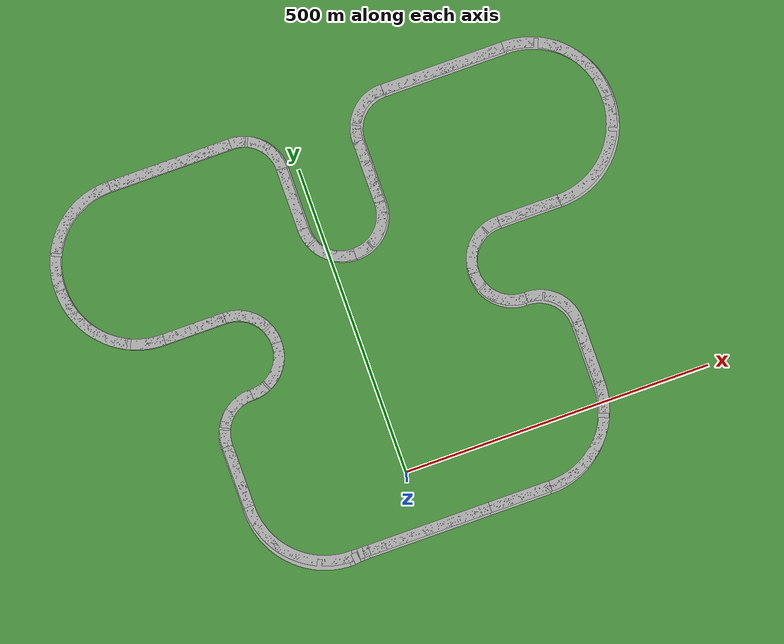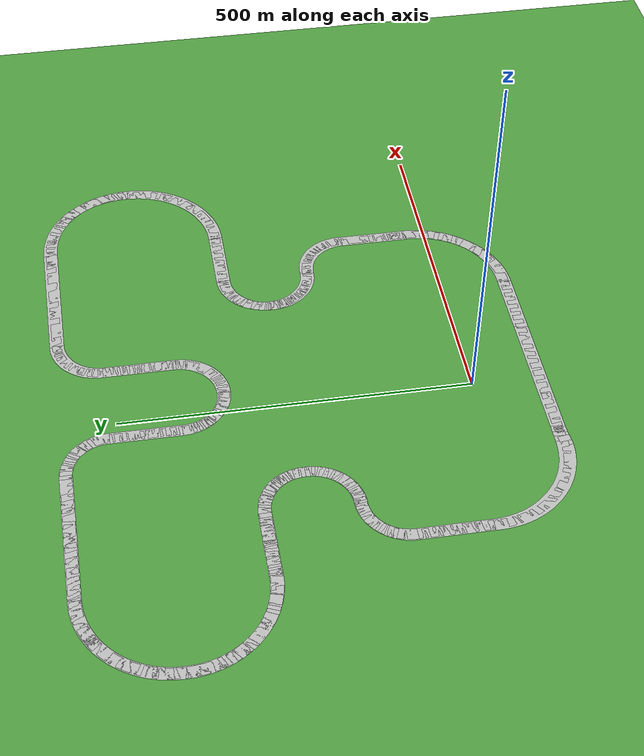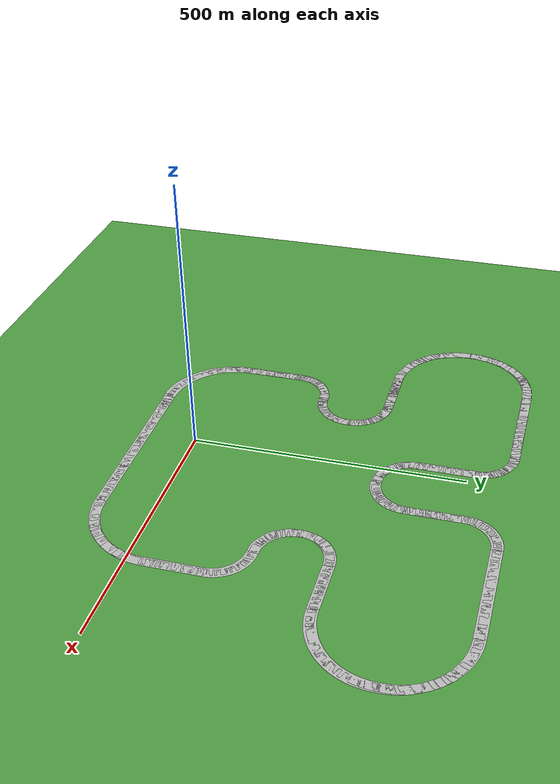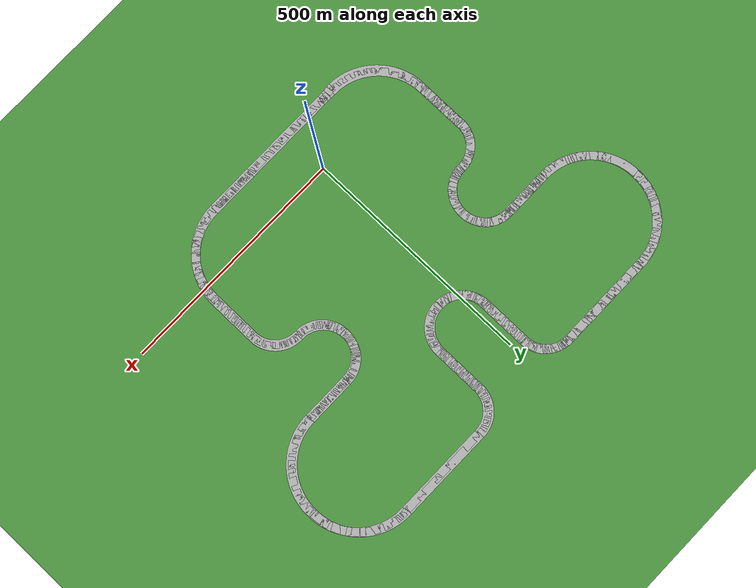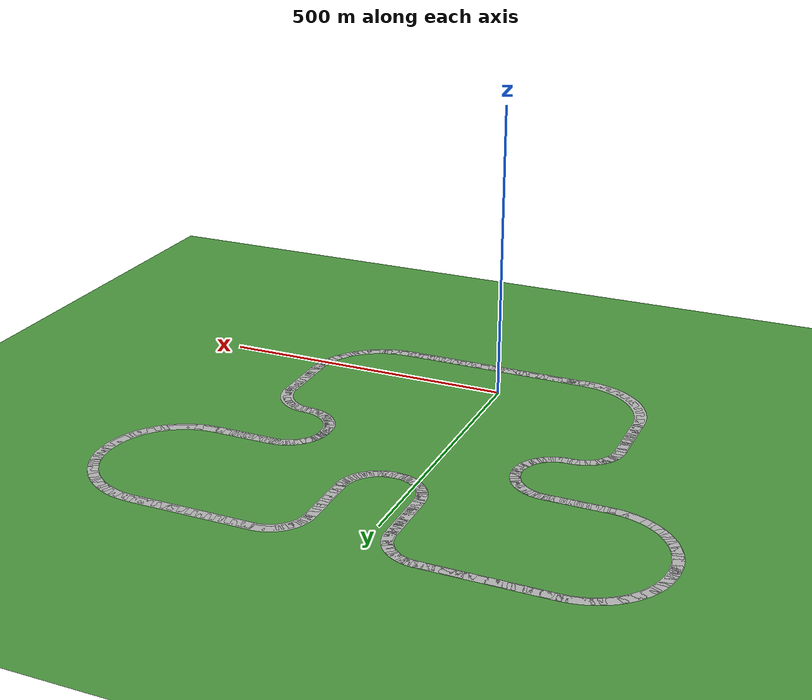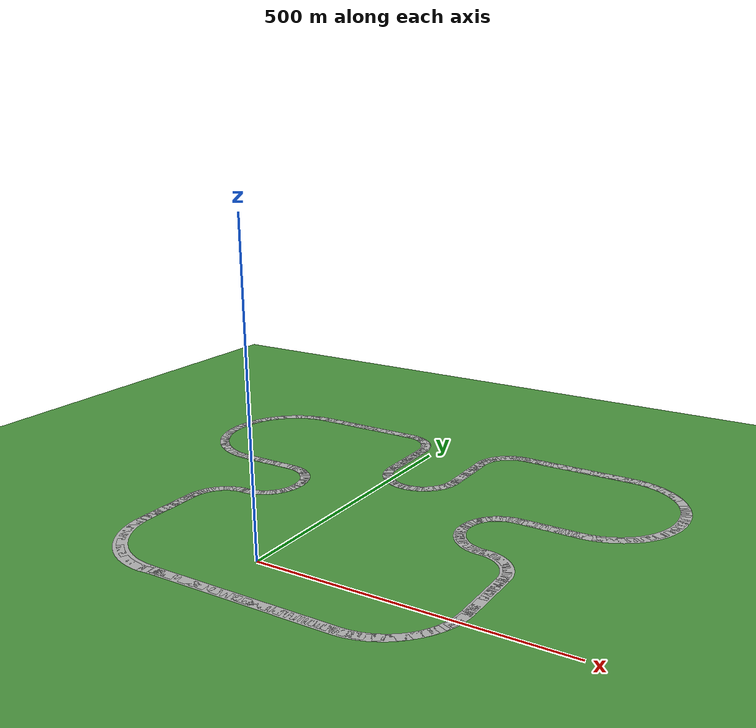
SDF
<sdf version="1.6">
 <world name="default">
  <light name="sun" type="directional">
   <pose>0 0 10 0 -0 0</pose>
   <diffuse>0.8 0.8 0.8 1</diffuse>
   <specular>0.2 0.2 0.2 1</specular>
   <attenuation>
    <range>1000</range>
    <constant>0.9</constant>
    <linear>0.01</linear>
    <quadratic>0.001</quadratic>
   </attenuation>
   <direction>-0.5 0.1 -0.9</direction>
  </light>
  <gravity>0 0 -9.8</gravity>
  <magnetic_field>6e-06 2.3e-05 -4.2e-05</magnetic_field>
  <atmosphere type="adiabatic"/>
  <physics name="default_physics" default="0" type="ode">
   <max_step_size>0.001</max_step_size>
   <real_time_factor>1</real_time_factor>
   <real_time_update_rate>1000</real_time_update_rate>
  </physics>
  <scene><ambient>0.4 0.4 0.4 1</ambient><background>0.7 0.7 0.7 1</background><shadows>1</shadows></scene>
  <audio><device>default</device></audio>
  <spherical_coordinates>
   <surface_model>EARTH_WGS84</surface_model>
   <latitude_deg>0</latitude_deg>
   <longitude_deg>0</longitude_deg>
   <elevation>0</elevation>
   <heading_deg>0</heading_deg>
  </spherical_coordinates>
  <model name="ground_plane">
   <pose>0 0 0 0 -0 3.14</pose>
   <static>1</static>
   <link name="link">
    <collision name="collision">
     <geometry><plane><normal>0 0 1</normal><size>100 100</size></plane></geometry>
     <surface><friction><ode><mu>100</mu><mu2>50</mu2></ode></friction></surface>
    </collision>
    <visual name="visual">
     <cast_shadows>0</cast_shadows>
     <geometry><plane><normal>0 0 1</normal><size>10000 10000</size></plane></geometry>
     <material>
      <script><uri>file://media/materials/scripts/ds_sim.material</uri><name>DSSim/GrassBackground</name></script>
     </material>
    </visual>
   </link>
  </model>
  <model name="straight100">
   <link name="link_0">
    <inertial>
     <mass>1</mass>
     <inertia>
      <ixx>0.166667</ixx>
      <ixy>0</ixy>
      <ixz>0</ixz>
      <iyy>0.166667</iyy>
      <iyz>0</iyz>
      <izz>0.166667</izz>
     </inertia>
    </inertial>
    <visual name="visual">
     <geometry><mesh><uri>/home/aws/Desktop/straight100.dae</uri><scale>1 1 1</scale></mesh></geometry>
    </visual>
    <collision name="collision">
     <geometry><mesh><uri>/home/aws/Desktop/straight100.dae</uri><scale>1 1 1</scale></mesh></geometry>
     <surface>
      <friction>
       <ode><mu>1</mu><mu2>1</mu2><fdir1>0 0 0</fdir1><slip1>0</slip1><slip2>0</slip2></ode>
       <torsional>
        <coefficient>1</coefficient>
        <patch_radius>0</patch_radius>
        <surface_radius>0</surface_radius>
        <use_patch_radius>1</use_patch_radius>
        <ode><slip>0</slip></ode>
       </torsional>
      </friction>
      <bounce><restitution_coefficient>0</restitution_coefficient><threshold>1e+06</threshold></bounce>
      <contact>
       <collide_without_contact>0</collide_without_contact>
       <collide_without_contact_bitmask>1</collide_without_contact_bitmask>
       <collide_bitmask>1</collide_bitmask>
       <ode>
        <soft_cfm>0</soft_cfm>
        <soft_erp>0.2</soft_erp>
        <kp>1e+13</kp>
        <kd>1</kd>
        <max_vel>0.01</max_vel>
        <min_depth>0</min_depth>
       </ode>
       <bullet>
        <split_impulse>1</split_impulse>
        <split_impulse_penetration_threshold>-0.01</split_impulse_penetration_threshold>
        <soft_cfm>0</soft_cfm>
        <soft_erp>0.2</soft_erp>
        <kp>1e+13</kp>
        <kd>1</kd>
       </bullet>
      </contact>
     </surface>
    </collision>
   </link>
   <static>1</static>
   <pose>104.925 -95.5492 0.05 0 -0 0</pose>
  </model>
  <model name="straight100_0">
   <link name="link_0">
    <inertial>
     <mass>1</mass>
     <inertia>
      <ixx>0.166667</ixx>
      <ixy>0</ixy>
      <ixz>0</ixz>
      <iyy>0.166667</iyy>
      <iyz>0</iyz>
      <izz>0.166667</izz>
     </inertia>
    </inertial>
    <visual name="visual">
     <geometry><mesh><uri>/home/aws/Desktop/straight100.dae</uri><scale>1 1 1</scale></mesh></geometry>
    </visual>
    <collision name="collision">
     <geometry><mesh><uri>/home/aws/Desktop/straight100.dae</uri><scale>1 1 1</scale></mesh></geometry>
     <surface>
      <friction>
       <ode><mu>1</mu><mu2>1</mu2><fdir1>0 0 0</fdir1><slip1>0</slip1><slip2>0</slip2></ode>
       <torsional>
        <coefficient>1</coefficient>
        <patch_radius>0</patch_radius>
        <surface_radius>0</surface_radius>
        <use_patch_radius>1</use_patch_radius>
        <ode><slip>0</slip></ode>
       </torsional>
      </friction>
      <bounce><restitution_coefficient>0</restitution_coefficient><threshold>1e+06</threshold></bounce>
      <contact>
       <collide_without_contact>0</collide_without_contact>
       <collide_without_contact_bitmask>1</collide_without_contact_bitmask>
       <collide_bitmask>1</collide_bitmask>
       <ode>
        <soft_cfm>0</soft_cfm>
        <soft_erp>0.2</soft_erp>
        <kp>1e+13</kp>
        <kd>1</kd>
        <max_vel>0.01</max_vel>
        <min_depth>0</min_depth>
       </ode>
       <bullet>
        <split_impulse>1</split_impulse>
        <split_impulse_penetration_threshold>-0.01</split_impulse_penetration_threshold>
        <soft_cfm>0</soft_cfm>
        <soft_erp>0.2</soft_erp>
        <kp>1e+13</kp>
        <kd>1</kd>
       </bullet>
      </contact>
     </surface>
    </collision>
   </link>
   <static>1</static>
   <pose>331.13 31.7233 0.05 0 -0 1.57</pose>
  </model>
  <model name="straight200">
   <link name="link_0">
    <inertial>
     <mass>1</mass>
     <inertia>
      <ixx>0.166667</ixx>
      <ixy>0</ixy>
      <ixz>0</ixz>
      <iyy>0.166667</iyy>
      <iyz>0</iyz>
      <izz>0.166667</izz>
     </inertia>
    </inertial>
    <visual name="visual">
     <geometry><mesh><uri>/home/aws/Desktop/straight200.dae</uri><scale>1 1 1</scale></mesh></geometry>
    </visual>
    <collision name="collision">
     <geometry><mesh><uri>/home/aws/Desktop/straight200.dae</uri><scale>1 1 1</scale></mesh></geometry>
     <surface>
      <friction>
       <ode><mu>1</mu><mu2>1</mu2><fdir1>0 0 0</fdir1><slip1>0</slip1><slip2>0</slip2></ode>
       <torsional>
        <coefficient>1</coefficient>
        <patch_radius>0</patch_radius>
        <surface_radius>0</surface_radius>
        <use_patch_radius>1</use_patch_radius>
        <ode><slip>0</slip></ode>
       </torsional>
      </friction>
      <bounce><restitution_coefficient>0</restitution_coefficient><threshold>1e+06</threshold></bounce>
      <contact>
       <collide_without_contact>0</collide_without_contact>
       <collide_without_contact_bitmask>1</collide_without_contact_bitmask>
       <collide_bitmask>1</collide_bitmask>
       <ode>
        <soft_cfm>0</soft_cfm>
        <soft_erp>0.2</soft_erp>
        <kp>1e+13</kp>
        <kd>1</kd>
        <max_vel>0.01</max_vel>
        <min_depth>0</min_depth>
       </ode>
       <bullet>
        <split_impulse>1</split_impulse>
        <split_impulse_penetration_threshold>-0.01</split_impulse_penetration_threshold>
        <soft_cfm>0</soft_cfm>
        <soft_erp>0.2</soft_erp>
        <kp>1e+13</kp>
        <kd>1</kd>
       </bullet>
      </contact>
     </surface>
    </collision>
   </link>
   <static>1</static>
   <pose>-94.9967 -95.5714 0.05 0 -0 0</pose>
  </model>
  <model name="curve200_L">
   <static>1</static>
   <link name="link">
    <inertial>
     <mass>1</mass>
     <inertia><ixx>1</ixx><iyy>1</iyy><izz>1</izz><ixy>0</ixy><ixz>0</ixz><iyz>0</iyz></inertia>
    </inertial>
    <collision name="collision">
     <geometry><mesh><uri>/home/aws/Desktop/curve200_L.dae</uri></mesh></geometry>
    </collision>
    <visual name="visual"><geometry><mesh><uri>/home/aws/Desktop/curve200_L.dae</uri></mesh></geometry></visual>
   </link>
   <pose>204.817 -96.9381 0.05 0 -0 0</pose>
  </model>
  <model name="curve100_L">
   <static>1</static>
   <link name="link">
    <inertial>
     <mass>1</mass>
     <inertia><ixx>1</ixx><iyy>1</iyy><izz>1</izz><ixy>0</ixy><ixz>0</ixz><iyz>0</iyz></inertia>
    </inertial>
    <collision name="collision">
     <geometry><mesh><uri>/home/aws/Desktop/curve100_L.dae</uri></mesh></geometry>
    </collision>
    <visual name="visual"><geometry><mesh><uri>/home/aws/Desktop/curve100_L.dae</uri></mesh></geometry></visual>
   </link>
   <pose>331.812 131.589 0.05 0 -0 1.57</pose>
  </model>
  <model name="curve100_R">
   <static>1</static>
   <link name="link">
    <inertial>
     <mass>1</mass>
     <inertia><ixx>1</ixx><iyy>1</iyy><izz>1</izz><ixy>0</ixy><ixz>0</ixz><iyz>0</iyz></inertia>
    </inertial>
    <collision name="collision">
     <geometry><mesh><uri>/home/aws/Desktop/curve100_R.dae</uri></mesh></geometry>
    </collision>
    <visual name="visual"><geometry><mesh><uri>/home/aws/Desktop/curve100_R.dae</uri></mesh></geometry></visual>
   </link>
   <pose>267.553 195.005 0.05 0 0 -3.11173</pose>
  </model>
  <model name="curve100_R_0">
   <static>1</static>
   <link name="link">
    <inertial>
     <mass>1</mass>
     <inertia><ixx>1</ixx><iyy>1</iyy><izz>1</izz><ixy>0</ixy><ixz>0</ixz><iyz>0</iyz></inertia>
    </inertial>
    <collision name="collision">
     <geometry><mesh><uri>/home/aws/Desktop/curve100_R.dae</uri></mesh></geometry>
    </collision>
    <visual name="visual"><geometry><mesh><uri>/home/aws/Desktop/curve100_R.dae</uri></mesh></geometry></visual>
   </link>
   <pose>204.052 257.367 0.05 0 -0 1.59756</pose>
  </model>
  <model name="straight100_1">
   <link name="link_0">
    <inertial>
     <mass>1</mass>
     <inertia>
      <ixx>0.166667</ixx>
      <ixy>0</ixy>
      <ixz>0</ixz>
      <iyy>0.166667</iyy>
      <iyz>0</iyz>
      <izz>0.166667</izz>
     </inertia>
    </inertial>
    <visual name="visual">
     <geometry><mesh><uri>/home/aws/Desktop/straight100.dae</uri><scale>1 1 1</scale></mesh></geometry>
    </visual>
    <collision name="collision">
     <geometry><mesh><uri>/home/aws/Desktop/straight100.dae</uri><scale>1 1 1</scale></mesh></geometry>
     <surface>
      <friction>
       <ode><mu>1</mu><mu2>1</mu2><fdir1>0 0 0</fdir1><slip1>0</slip1><slip2>0</slip2></ode>
       <torsional>
        <coefficient>1</coefficient>
        <patch_radius>0</patch_radius>
        <surface_radius>0</surface_radius>
        <use_patch_radius>1</use_patch_radius>
        <ode><slip>0</slip></ode>
       </torsional>
      </friction>
      <bounce><restitution_coefficient>0</restitution_coefficient><threshold>1e+06</threshold></bounce>
      <contact>
       <collide_without_contact>0</collide_without_contact>
       <collide_without_contact_bitmask>1</collide_without_contact_bitmask>
       <collide_bitmask>1</collide_bitmask>
       <ode>
        <soft_cfm>0</soft_cfm>
        <soft_erp>0.2</soft_erp>
        <kp>1e+13</kp>
        <kd>1</kd>
        <max_vel>0.01</max_vel>
        <min_depth>0</min_depth>
       </ode>
       <bullet>
        <split_impulse>1</split_impulse>
        <split_impulse_penetration_threshold>-0.01</split_impulse_penetration_threshold>
        <soft_cfm>0</soft_cfm>
        <soft_erp>0.2</soft_erp>
        <kp>1e+13</kp>
        <kd>1</kd>
       </bullet>
      </contact>
     </surface>
    </collision>
   </link>
   <static>1</static>
   <pose>266.582 321.304 0.05 0 -0 0</pose>
  </model>
  <model name="curve200_L_0">
   <static>1</static>
   <link name="link">
    <inertial>
     <mass>1</mass>
     <inertia><ixx>1</ixx><iyy>1</iyy><izz>1</izz><ixy>0</ixy><ixz>0</ixz><iyz>0</iyz></inertia>
    </inertial>
    <collision name="collision">
     <geometry><mesh><uri>/home/aws/Desktop/curve200_L.dae</uri></mesh></geometry>
    </collision>
    <visual name="visual"><geometry><mesh><uri>/home/aws/Desktop/curve200_L.dae</uri></mesh></geometry></visual>
   </link>
   <pose>364.798 319.895 0.05 0 -0 0</pose>
  </model>
  <model name="curve200_L_1">
   <static>1</static>
   <link name="link">
    <inertial>
     <mass>1</mass>
     <inertia><ixx>1</ixx><iyy>1</iyy><izz>1</izz><ixy>0</ixy><ixz>0</ixz><iyz>0</iyz></inertia>
    </inertial>
    <collision name="collision">
     <geometry><mesh><uri>/home/aws/Desktop/curve200_L.dae</uri></mesh></geometry>
    </collision>
    <visual name="visual"><geometry><mesh><uri>/home/aws/Desktop/curve200_L.dae</uri></mesh></geometry></visual>
   </link>
   <pose>492.497 448.584 0.05 0 -0 1.57</pose>
  </model>
  <model name="straight200_0">
   <link name="link_0">
    <inertial>
     <mass>1</mass>
     <inertia>
      <ixx>0.166667</ixx>
      <ixy>0</ixy>
      <ixz>0</ixz>
      <iyy>0.166667</iyy>
      <iyz>0</iyz>
      <izz>0.166667</izz>
     </inertia>
    </inertial>
    <visual name="visual">
     <geometry><mesh><uri>/home/aws/Desktop/straight200.dae</uri><scale>1 1 1</scale></mesh></geometry>
    </visual>
    <collision name="collision">
     <geometry><mesh><uri>/home/aws/Desktop/straight200.dae</uri><scale>1 1 1</scale></mesh></geometry>
     <surface>
      <friction>
       <ode><mu>1</mu><mu2>1</mu2><fdir1>0 0 0</fdir1><slip1>0</slip1><slip2>0</slip2></ode>
       <torsional>
        <coefficient>1</coefficient>
        <patch_radius>0</patch_radius>
        <surface_radius>0</surface_radius>
        <use_patch_radius>1</use_patch_radius>
        <ode><slip>0</slip></ode>
       </torsional>
      </friction>
      <bounce><restitution_coefficient>0</restitution_coefficient><threshold>1e+06</threshold></bounce>
      <contact>
       <collide_without_contact>0</collide_without_contact>
       <collide_without_contact_bitmask>1</collide_without_contact_bitmask>
       <collide_bitmask>1</collide_bitmask>
       <ode>
        <soft_cfm>0</soft_cfm>
        <soft_erp>0.2</soft_erp>
        <kp>1e+13</kp>
        <kd>1</kd>
        <max_vel>0.01</max_vel>
        <min_depth>0</min_depth>
       </ode>
       <bullet>
        <split_impulse>1</split_impulse>
        <split_impulse_penetration_threshold>-0.01</split_impulse_penetration_threshold>
        <soft_cfm>0</soft_cfm>
        <soft_erp>0.2</soft_erp>
        <kp>1e+13</kp>
        <kd>1</kd>
       </bullet>
      </contact>
     </surface>
    </collision>
   </link>
   <static>1</static>
   <pose>363.961 575.015 0.05 0 -0 3.14</pose>
  </model>
  <model name="straight200_1">
   <link name="link_0">
    <inertial>
     <mass>1</mass>
     <inertia>
      <ixx>0.166667</ixx>
      <ixy>0</ixy>
      <ixz>0</ixz>
      <iyy>0.166667</iyy>
      <iyz>0</iyz>
      <izz>0.166667</izz>
     </inertia>
    </inertial>
    <visual name="visual">
     <geometry><mesh><uri>/home/aws/Desktop/straight200.dae</uri><scale>1 1 1</scale></mesh></geometry>
    </visual>
    <collision name="collision">
     <geometry><mesh><uri>/home/aws/Desktop/straight200.dae</uri><scale>1 1 1</scale></mesh></geometry>
     <surface>
      <friction>
       <ode><mu>1</mu><mu2>1</mu2><fdir1>0 0 0</fdir1><slip1>0</slip1><slip2>0</slip2></ode>
       <torsional>
        <coefficient>1</coefficient>
        <patch_radius>0</patch_radius>
        <surface_radius>0</surface_radius>
        <use_patch_radius>1</use_patch_radius>
        <ode><slip>0</slip></ode>
       </torsional>
      </friction>
      <bounce><restitution_coefficient>0</restitution_coefficient><threshold>1e+06</threshold></bounce>
      <contact>
       <collide_without_contact>0</collide_without_contact>
       <collide_without_contact_bitmask>1</collide_without_contact_bitmask>
       <collide_bitmask>1</collide_bitmask>
       <ode>
        <soft_cfm>0</soft_cfm>
        <soft_erp>0.2</soft_erp>
        <kp>1e+13</kp>
        <kd>1</kd>
        <max_vel>0.01</max_vel>
        <min_depth>0</min_depth>
       </ode>
       <bullet>
        <split_impulse>1</split_impulse>
        <split_impulse_penetration_threshold>-0.01</split_impulse_penetration_threshold>
        <soft_cfm>0</soft_cfm>
        <soft_erp>0.2</soft_erp>
        <kp>1e+13</kp>
        <kd>1</kd>
       </bullet>
      </contact>
     </surface>
    </collision>
   </link>
   <static>1</static>
   <pose>-88.5359 574.77 0.05 0 -0 3.14</pose>
  </model>
  <model name="curve100_L_0">
   <static>1</static>
   <link name="link">
    <inertial>
     <mass>1</mass>
     <inertia><ixx>1</ixx><iyy>1</iyy><izz>1</izz><ixy>0</ixy><ixz>0</ixz><iyz>0</iyz></inertia>
    </inertial>
    <collision name="collision">
     <geometry><mesh><uri>/home/aws/Desktop/curve100_L.dae</uri></mesh></geometry>
    </collision>
    <visual name="visual"><geometry><mesh><uri>/home/aws/Desktop/curve100_L.dae</uri></mesh></geometry></visual>
   </link>
   <pose>164.295 575.928 0.05 0 -0 3.14</pose>
  </model>
  <model name="straight100_2">
   <link name="link_0">
    <inertial>
     <mass>1</mass>
     <inertia>
      <ixx>0.166667</ixx>
      <ixy>0</ixy>
      <ixz>0</ixz>
      <iyy>0.166667</iyy>
      <iyz>0</iyz>
      <izz>0.166667</izz>
     </inertia>
    </inertial>
    <visual name="visual">
     <geometry><mesh><uri>/home/aws/Desktop/straight100.dae</uri><scale>1 1 1</scale></mesh></geometry>
    </visual>
    <collision name="collision">
     <geometry><mesh><uri>/home/aws/Desktop/straight100.dae</uri><scale>1 1 1</scale></mesh></geometry>
     <surface>
      <friction>
       <ode><mu>1</mu><mu2>1</mu2><fdir1>0 0 0</fdir1><slip1>0</slip1><slip2>0</slip2></ode>
       <torsional>
        <coefficient>1</coefficient>
        <patch_radius>0</patch_radius>
        <surface_radius>0</surface_radius>
        <use_patch_radius>1</use_patch_radius>
        <ode><slip>0</slip></ode>
       </torsional>
      </friction>
      <bounce><restitution_coefficient>0</restitution_coefficient><threshold>1e+06</threshold></bounce>
      <contact>
       <collide_without_contact>0</collide_without_contact>
       <collide_without_contact_bitmask>1</collide_without_contact_bitmask>
       <collide_bitmask>1</collide_bitmask>
       <ode>
        <soft_cfm>0</soft_cfm>
        <soft_erp>0.2</soft_erp>
        <kp>1e+13</kp>
        <kd>1</kd>
        <max_vel>0.01</max_vel>
        <min_depth>0</min_depth>
       </ode>
       <bullet>
        <split_impulse>1</split_impulse>
        <split_impulse_penetration_threshold>-0.01</split_impulse_penetration_threshold>
        <soft_cfm>0</soft_cfm>
        <soft_erp>0.2</soft_erp>
        <kp>1e+13</kp>
        <kd>1</kd>
       </bullet>
      </contact>
     </surface>
    </collision>
   </link>
   <static>1</static>
   <pose>101.463 511.908 0.05 0 0 -1.57</pose>
  </model>
  <model name="curve100_R_1">
   <static>1</static>
   <link name="link">
    <inertial>
     <mass>1</mass>
     <inertia><ixx>1</ixx><iyy>1</iyy><izz>1</izz><ixy>0</ixy><ixz>0</ixz><iyz>0</iyz></inertia>
    </inertial>
    <collision name="collision">
     <geometry><mesh><uri>/home/aws/Desktop/curve100_R.dae</uri></mesh></geometry>
    </collision>
    <visual name="visual"><geometry><mesh><uri>/home/aws/Desktop/curve100_R.dae</uri></mesh></geometry></visual>
   </link>
   <pose>100.907 411.93 0.05 0 0 -1.5463</pose>
  </model>
  <model name="curve100_R_2">
   <static>1</static>
   <link name="link">
    <inertial>
     <mass>1</mass>
     <inertia><ixx>1</ixx><iyy>1</iyy><izz>1</izz><ixy>0</ixy><ixz>0</ixz><iyz>0</iyz></inertia>
    </inertial>
    <collision name="collision">
     <geometry><mesh><uri>/home/aws/Desktop/curve100_R.dae</uri></mesh></geometry>
    </collision>
    <visual name="visual"><geometry><mesh><uri>/home/aws/Desktop/curve100_R.dae</uri></mesh></geometry></visual>
   </link>
   <pose>38.1624 348.751 0.05 0 0 -3.11898</pose>
  </model>
  <model name="straight100_3">
   <link name="link_0">
    <inertial>
     <mass>1</mass>
     <inertia>
      <ixx>0.166667</ixx>
      <ixy>0</ixy>
      <ixz>0</ixz>
      <iyy>0.166667</iyy>
      <iyz>0</iyz>
      <izz>0.166667</izz>
     </inertia>
    </inertial>
    <visual name="visual">
     <geometry><mesh><uri>/home/aws/Desktop/straight100.dae</uri><scale>1 1 1</scale></mesh></geometry>
    </visual>
    <collision name="collision">
     <geometry><mesh><uri>/home/aws/Desktop/straight100.dae</uri><scale>1 1 1</scale></mesh></geometry>
     <surface>
      <friction>
       <ode><mu>1</mu><mu2>1</mu2><fdir1>0 0 0</fdir1><slip1>0</slip1><slip2>0</slip2></ode>
       <torsional>
        <coefficient>1</coefficient>
        <patch_radius>0</patch_radius>
        <surface_radius>0</surface_radius>
        <use_patch_radius>1</use_patch_radius>
        <ode><slip>0</slip></ode>
       </torsional>
      </friction>
      <bounce><restitution_coefficient>0</restitution_coefficient><threshold>1e+06</threshold></bounce>
      <contact>
       <collide_without_contact>0</collide_without_contact>
       <collide_without_contact_bitmask>1</collide_without_contact_bitmask>
       <collide_bitmask>1</collide_bitmask>
       <ode>
        <soft_cfm>0</soft_cfm>
        <soft_erp>0.2</soft_erp>
        <kp>1e+13</kp>
        <kd>1</kd>
        <max_vel>0.01</max_vel>
        <min_depth>0</min_depth>
       </ode>
       <bullet>
        <split_impulse>1</split_impulse>
        <split_impulse_penetration_threshold>-0.01</split_impulse_penetration_threshold>
        <soft_cfm>0</soft_cfm>
        <soft_erp>0.2</soft_erp>
        <kp>1e+13</kp>
        <kd>1</kd>
       </bullet>
      </contact>
     </surface>
    </collision>
   </link>
   <static>1</static>
   <pose>-25.5193 411.604 0.05 0 -0 1.57</pose>
  </model>
  <model name="curve100_L_1">
   <static>1</static>
   <link name="link">
    <inertial>
     <mass>1</mass>
     <inertia><ixx>1</ixx><iyy>1</iyy><izz>1</izz><ixy>0</ixy><ixz>0</ixz><iyz>0</iyz></inertia>
    </inertial>
    <collision name="collision">
     <geometry><mesh><uri>/home/aws/Desktop/curve100_L.dae</uri></mesh></geometry>
    </collision>
    <visual name="visual"><geometry><mesh><uri>/home/aws/Desktop/curve100_L.dae</uri></mesh></geometry></visual>
   </link>
   <pose>-24.8107 511.511 0.05 0 -0 1.56339</pose>
  </model>
  <model name="curve200_L_2">
   <static>1</static>
   <link name="link">
    <inertial>
     <mass>1</mass>
     <inertia><ixx>1</ixx><iyy>1</iyy><izz>1</izz><ixy>0</ixy><ixz>0</ixz><iyz>0</iyz></inertia>
    </inertial>
    <collision name="collision">
     <geometry><mesh><uri>/home/aws/Desktop/curve200_L.dae</uri></mesh></geometry>
    </collision>
    <visual name="visual"><geometry><mesh><uri>/home/aws/Desktop/curve200_L.dae</uri></mesh></geometry></visual>
   </link>
   <pose>-288.013 576.432 0.05 0 -0 3.14</pose>
  </model>
  <model name="curve200_L_3">
   <static>1</static>
   <link name="link">
    <inertial>
     <mass>1</mass>
     <inertia><ixx>1</ixx><iyy>1</iyy><izz>1</izz><ixy>0</ixy><ixz>0</ixz><iyz>0</iyz></inertia>
    </inertial>
    <collision name="collision">
     <geometry><mesh><uri>/home/aws/Desktop/curve200_L.dae</uri></mesh></geometry>
    </collision>
    <visual name="visual"><geometry><mesh><uri>/home/aws/Desktop/curve200_L.dae</uri></mesh></geometry></visual>
   </link>
   <pose>-415.91 447.969 0.05 0 0 -1.57</pose>
  </model>
  <model name="straight100_4">
   <link name="link_0">
    <inertial>
     <mass>1</mass>
     <inertia>
      <ixx>0.166667</ixx>
      <ixy>0</ixy>
      <ixz>0</ixz>
      <iyy>0.166667</iyy>
      <iyz>0</iyz>
      <izz>0.166667</izz>
     </inertia>
    </inertial>
    <visual name="visual">
     <geometry><mesh><uri>/home/aws/Desktop/straight100.dae</uri><scale>1 1 1</scale></mesh></geometry>
    </visual>
    <collision name="collision">
     <geometry><mesh><uri>/home/aws/Desktop/straight100.dae</uri><scale>1 1 1</scale></mesh></geometry>
     <surface>
      <friction>
       <ode><mu>1</mu><mu2>1</mu2><fdir1>0 0 0</fdir1><slip1>0</slip1><slip2>0</slip2></ode>
       <torsional>
        <coefficient>1</coefficient>
        <patch_radius>0</patch_radius>
        <surface_radius>0</surface_radius>
        <use_patch_radius>1</use_patch_radius>
        <ode><slip>0</slip></ode>
       </torsional>
      </friction>
      <bounce><restitution_coefficient>0</restitution_coefficient><threshold>1e+06</threshold></bounce>
      <contact>
       <collide_without_contact>0</collide_without_contact>
       <collide_without_contact_bitmask>1</collide_without_contact_bitmask>
       <collide_bitmask>1</collide_bitmask>
       <ode>
        <soft_cfm>0</soft_cfm>
        <soft_erp>0.2</soft_erp>
        <kp>1e+13</kp>
        <kd>1</kd>
        <max_vel>0.01</max_vel>
        <min_depth>0</min_depth>
       </ode>
       <bullet>
        <split_impulse>1</split_impulse>
        <split_impulse_penetration_threshold>-0.01</split_impulse_penetration_threshold>
        <soft_cfm>0</soft_cfm>
        <soft_erp>0.2</soft_erp>
        <kp>1e+13</kp>
        <kd>1</kd>
       </bullet>
      </contact>
     </surface>
    </collision>
   </link>
   <static>1</static>
   <pose>-287.19 321.773 0.05 0 -0 0</pose>
  </model>
  <model name="curve100_R_3">
   <static>1</static>
   <link name="link">
    <inertial>
     <mass>1</mass>
     <inertia><ixx>1</ixx><iyy>1</iyy><izz>1</izz><ixy>0</ixy><ixz>0</ixz><iyz>0</iyz></inertia>
    </inertial>
    <collision name="collision">
     <geometry><mesh><uri>/home/aws/Desktop/curve100_R.dae</uri></mesh></geometry>
    </collision>
    <visual name="visual"><geometry><mesh><uri>/home/aws/Desktop/curve100_R.dae</uri></mesh></geometry></visual>
   </link>
   <pose>-187.235 321.138 0.05 0 -0 0.020116</pose>
  </model>
  <model name="curve100_R_4">
   <static>1</static>
   <link name="link">
    <inertial>
     <mass>1</mass>
     <inertia><ixx>1</ixx><iyy>1</iyy><izz>1</izz><ixy>0</ixy><ixz>0</ixz><iyz>0</iyz></inertia>
    </inertial>
    <collision name="collision">
     <geometry><mesh><uri>/home/aws/Desktop/curve100_R.dae</uri></mesh></geometry>
    </collision>
    <visual name="visual"><geometry><mesh><uri>/home/aws/Desktop/curve100_R.dae</uri></mesh></geometry></visual>
   </link>
   <pose>-124.338 258.149 0.05 0 0 -1.54825</pose>
  </model>
  <model name="curve100_L_2">
   <static>1</static>
   <link name="link">
    <inertial>
     <mass>1</mass>
     <inertia><ixx>1</ixx><iyy>1</iyy><izz>1</izz><ixy>0</ixy><ixz>0</ixz><iyz>0</iyz></inertia>
    </inertial>
    <collision name="collision">
     <geometry><mesh><uri>/home/aws/Desktop/curve100_L.dae</uri></mesh></geometry>
    </collision>
    <visual name="visual"><geometry><mesh><uri>/home/aws/Desktop/curve100_L.dae</uri></mesh></geometry></visual>
   </link>
   <pose>-186.669 195.084 0.05 0 -0 3.13696</pose>
  </model>
  <model name="straight100_6">
   <link name="link_0">
    <inertial>
     <mass>1</mass>
     <inertia>
      <ixx>0.166667</ixx>
      <ixy>0</ixy>
      <ixz>0</ixz>
      <iyy>0.166667</iyy>
      <iyz>0</iyz>
      <izz>0.166667</izz>
     </inertia>
    </inertial>
    <visual name="visual">
     <geometry><mesh><uri>/home/aws/Desktop/straight100.dae</uri><scale>1 1 1</scale></mesh></geometry>
    </visual>
    <collision name="collision">
     <geometry><mesh><uri>/home/aws/Desktop/straight100.dae</uri><scale>1 1 1</scale></mesh></geometry>
     <surface>
      <friction>
       <ode><mu>1</mu><mu2>1</mu2><fdir1>0 0 0</fdir1><slip1>0</slip1><slip2>0</slip2></ode>
       <torsional>
        <coefficient>1</coefficient>
        <patch_radius>0</patch_radius>
        <surface_radius>0</surface_radius>
        <use_patch_radius>1</use_patch_radius>
        <ode><slip>0</slip></ode>
       </torsional>
      </friction>
      <bounce><restitution_coefficient>0</restitution_coefficient><threshold>1e+06</threshold></bounce>
      <contact>
       <collide_without_contact>0</collide_without_contact>
       <collide_without_contact_bitmask>1</collide_without_contact_bitmask>
       <collide_bitmask>1</collide_bitmask>
       <ode>
        <soft_cfm>0</soft_cfm>
        <soft_erp>0.2</soft_erp>
        <kp>1e+13</kp>
        <kd>1</kd>
        <max_vel>0.01</max_vel>
        <min_depth>0</min_depth>
       </ode>
       <bullet>
        <split_impulse>1</split_impulse>
        <split_impulse_penetration_threshold>-0.01</split_impulse_penetration_threshold>
        <soft_cfm>0</soft_cfm>
        <soft_erp>0.2</soft_erp>
        <kp>1e+13</kp>
        <kd>1</kd>
       </bullet>
      </contact>
     </surface>
    </collision>
   </link>
   <static>1</static>
   <pose>-249.691 131.106 0.05 0 0 -1.57</pose>
  </model>
  <model name="curve200_L_4">
   <static>1</static>
   <link name="link">
    <inertial>
     <mass>1</mass>
     <inertia><ixx>1</ixx><iyy>1</iyy><izz>1</izz><ixy>0</ixy><ixz>0</ixz><iyz>0</iyz></inertia>
    </inertial>
    <collision name="collision">
     <geometry><mesh><uri>/home/aws/Desktop/curve200_L.dae</uri></mesh></geometry>
    </collision>
    <visual name="visual"><geometry><mesh><uri>/home/aws/Desktop/curve200_L.dae</uri></mesh></geometry></visual>
   </link>
   <pose>-250.998 31.1021 0.05 0 0 -1.57</pose>
  </model>
  <model name="connecter_10m_with_lines">
   <link name="link_1">
    <inertial>
     <mass>1</mass>
     <inertia>
      <ixx>0.166667</ixx>
      <ixy>0</ixy>
      <ixz>0</ixz>
      <iyy>0.166667</iyy>
      <iyz>0</iyz>
      <izz>0.166667</izz>
     </inertia>
    </inertial>
    <visual name="visual">
     <geometry>
      <mesh><uri>/home/aws/Desktop/connecter_10m_with_lines.dae</uri><scale>1 1 1</scale></mesh>
     </geometry>
    </visual>
    <collision name="collision">
     <geometry>
      <mesh><uri>/home/aws/Desktop/connecter_10m_with_lines.dae</uri><scale>1 1 1</scale></mesh>
     </geometry>
     <surface>
      <friction>
       <ode><mu>1</mu><mu2>1</mu2><fdir1>0 0 0</fdir1><slip1>0</slip1><slip2>0</slip2></ode>
       <torsional>
        <coefficient>1</coefficient>
        <patch_radius>0</patch_radius>
        <surface_radius>0</surface_radius>
        <use_patch_radius>1</use_patch_radius>
        <ode><slip>0</slip></ode>
       </torsional>
      </friction>
      <bounce><restitution_coefficient>0</restitution_coefficient><threshold>1e+06</threshold></bounce>
      <contact>
       <collide_without_contact>0</collide_without_contact>
       <collide_without_contact_bitmask>1</collide_without_contact_bitmask>
       <collide_bitmask>1</collide_bitmask>
       <ode>
        <soft_cfm>0</soft_cfm>
        <soft_erp>0.2</soft_erp>
        <kp>1e+13</kp>
        <kd>1</kd>
        <max_vel>0.01</max_vel>
        <min_depth>0</min_depth>
       </ode>
       <bullet>
        <split_impulse>1</split_impulse>
        <split_impulse_penetration_threshold>-0.01</split_impulse_penetration_threshold>
        <soft_cfm>0</soft_cfm>
        <soft_erp>0.2</soft_erp>
        <kp>1e+13</kp>
        <kd>1</kd>
       </bullet>
      </contact>
     </surface>
    </collision>
   </link>
   <static>1</static>
   <pose>-104.691 -95.4061 0.05 0 0 -0.020654</pose>
  </model>
  <model name="connecter_10m_with_lines_0">
   <link name="link_1">
    <inertial>
     <mass>1</mass>
     <inertia>
      <ixx>0.166667</ixx>
      <ixy>0</ixy>
      <ixz>0</ixz>
      <iyy>0.166667</iyy>
      <iyz>0</iyz>
      <izz>0.166667</izz>
     </inertia>
    </inertial>
    <visual name="visual">
     <geometry>
      <mesh><uri>/home/aws/Desktop/connecter_10m_with_lines.dae</uri><scale>1 1 1</scale></mesh>
     </geometry>
    </visual>
    <collision name="collision">
     <geometry>
      <mesh><uri>/home/aws/Desktop/connecter_10m_with_lines.dae</uri><scale>1 1 1</scale></mesh>
     </geometry>
     <surface>
      <friction>
       <ode><mu>1</mu><mu2>1</mu2><fdir1>0 0 0</fdir1><slip1>0</slip1><slip2>0</slip2></ode>
       <torsional>
        <coefficient>1</coefficient>
        <patch_radius>0</patch_radius>
        <surface_radius>0</surface_radius>
        <use_patch_radius>1</use_patch_radius>
        <ode><slip>0</slip></ode>
       </torsional>
      </friction>
      <bounce><restitution_coefficient>0</restitution_coefficient><threshold>1e+06</threshold></bounce>
      <contact>
       <collide_without_contact>0</collide_without_contact>
       <collide_without_contact_bitmask>1</collide_without_contact_bitmask>
       <collide_bitmask>1</collide_bitmask>
       <ode>
        <soft_cfm>0</soft_cfm>
        <soft_erp>0.2</soft_erp>
        <kp>1e+13</kp>
        <kd>1</kd>
        <max_vel>0.01</max_vel>
        <min_depth>0</min_depth>
       </ode>
       <bullet>
        <split_impulse>1</split_impulse>
        <split_impulse_penetration_threshold>-0.01</split_impulse_penetration_threshold>
        <soft_cfm>0</soft_cfm>
        <soft_erp>0.2</soft_erp>
        <kp>1e+13</kp>
        <kd>1</kd>
       </bullet>
      </contact>
     </surface>
    </collision>
   </link>
   <static>1</static>
   <pose>-113.247 -95.3718 0.05 0 0 -0.007108</pose>
  </model>
  <model name="connecter_10m_without_lines">
   <link name="link_0">
    <inertial>
     <mass>1</mass>
     <inertia>
      <ixx>0.166667</ixx>
      <ixy>0</ixy>
      <ixz>0</ixz>
      <iyy>0.166667</iyy>
      <iyz>0</iyz>
      <izz>0.166667</izz>
     </inertia>
    </inertial>
    <visual name="visual">
     <geometry>
      <mesh><uri>/home/aws/Desktop/connecter_10m_without_lines.dae</uri><scale>1 1 1</scale></mesh>
     </geometry>
    </visual>
    <collision name="collision">
     <geometry>
      <mesh><uri>/home/aws/Desktop/connecter_10m_without_lines.dae</uri><scale>1 1 1</scale></mesh>
     </geometry>
     <surface>
      <friction>
       <ode><mu>1</mu><mu2>1</mu2><fdir1>0 0 0</fdir1><slip1>0</slip1><slip2>0</slip2></ode>
       <torsional>
        <coefficient>1</coefficient>
        <patch_radius>0</patch_radius>
        <surface_radius>0</surface_radius>
        <use_patch_radius>1</use_patch_radius>
        <ode><slip>0</slip></ode>
       </torsional>
      </friction>
      <bounce><restitution_coefficient>0</restitution_coefficient><threshold>1e+06</threshold></bounce>
      <contact>
       <collide_without_contact>0</collide_without_contact>
       <collide_without_contact_bitmask>1</collide_without_contact_bitmask>
       <collide_bitmask>1</collide_bitmask>
       <ode>
        <soft_cfm>0</soft_cfm>
        <soft_erp>0.2</soft_erp>
        <kp>1e+13</kp>
        <kd>1</kd>
        <max_vel>0.01</max_vel>
        <min_depth>0</min_depth>
       </ode>
       <bullet>
        <split_impulse>1</split_impulse>
        <split_impulse_penetration_threshold>-0.01</split_impulse_penetration_threshold>
        <soft_cfm>0</soft_cfm>
        <soft_erp>0.2</soft_erp>
        <kp>1e+13</kp>
        <kd>1</kd>
       </bullet>
      </contact>
     </surface>
    </collision>
   </link>
   <static>1</static>
   <pose>-122.851 -95.1236 0.05 0 0 -0.030598</pose>
  </model>
  <model name="straight200_2">
   <link name="link_0">
    <inertial>
     <mass>1</mass>
     <inertia>
      <ixx>0.166667</ixx>
      <ixy>0</ixy>
      <ixz>0</ixz>
      <iyy>0.166667</iyy>
      <iyz>0</iyz>
      <izz>0.166667</izz>
     </inertia>
    </inertial>
    <visual name="visual">
     <geometry>
      <mesh>
       <uri>/home/aws/oscar/catkin_ws/src/fusion/aws_models/blender_files/straight200.dae</uri>
       <scale>1 1 1</scale>
      </mesh>
     </geometry>
    </visual>
    <collision name="collision">
     <geometry>
      <mesh>
       <uri>/home/aws/oscar/catkin_ws/src/fusion/aws_models/blender_files/straight200.dae</uri>
       <scale>1 1 1</scale>
      </mesh>
     </geometry>
     <surface>
      <friction>
       <ode><mu>1</mu><mu2>1</mu2><fdir1>0 0 0</fdir1><slip1>0</slip1><slip2>0</slip2></ode>
       <torsional>
        <coefficient>1</coefficient>
        <patch_radius>0</patch_radius>
        <surface_radius>0</surface_radius>
        <use_patch_radius>1</use_patch_radius>
        <ode><slip>0</slip></ode>
       </torsional>
      </friction>
      <bounce><restitution_coefficient>0</restitution_coefficient><threshold>1e+06</threshold></bounce>
      <contact>
       <collide_without_contact>0</collide_without_contact>
       <collide_without_contact_bitmask>1</collide_without_contact_bitmask>
       <collide_bitmask>1</collide_bitmask>
       <ode>
        <soft_cfm>0</soft_cfm>
        <soft_erp>0.2</soft_erp>
        <kp>1e+13</kp>
        <kd>1</kd>
        <max_vel>0.01</max_vel>
        <min_depth>0</min_depth>
       </ode>
       <bullet>
        <split_impulse>1</split_impulse>
        <split_impulse_penetration_threshold>-0.01</split_impulse_penetration_threshold>
        <soft_cfm>0</soft_cfm>
        <soft_erp>0.2</soft_erp>
        <kp>1e+13</kp>
        <kd>1</kd>
       </bullet>
      </contact>
     </surface>
    </collision>
   </link>
   <static>1</static>
   <pose>-97.6786 -99.0813 0.05 0 -0 0</pose>
  </model>
  <model name="straight100_5">
   <link name="link_1">
    <inertial>
     <mass>1</mass>
     <inertia>
      <ixx>0.166667</ixx>
      <ixy>0</ixy>
      <ixz>0</ixz>
      <iyy>0.166667</iyy>
      <iyz>0</iyz>
      <izz>0.166667</izz>
     </inertia>
    </inertial>
    <visual name="visual">
     <geometry>
      <mesh>
       <uri>/home/aws/oscar/catkin_ws/src/fusion/aws_models/blender_files/straight100.dae</uri>
       <scale>1 1 1</scale>
      </mesh>
     </geometry>
    </visual>
    <collision name="collision">
     <geometry>
      <mesh>
       <uri>/home/aws/oscar/catkin_ws/src/fusion/aws_models/blender_files/straight100.dae</uri>
       <scale>1 1 1</scale>
      </mesh>
     </geometry>
     <surface>
      <friction>
       <ode><mu>1</mu><mu2>1</mu2><fdir1>0 0 0</fdir1><slip1>0</slip1><slip2>0</slip2></ode>
       <torsional>
        <coefficient>1</coefficient>
        <patch_radius>0</patch_radius>
        <surface_radius>0</surface_radius>
        <use_patch_radius>1</use_patch_radius>
        <ode><slip>0</slip></ode>
       </torsional>
      </friction>
      <bounce><restitution_coefficient>0</restitution_coefficient><threshold>1e+06</threshold></bounce>
      <contact>
       <collide_without_contact>0</collide_without_contact>
       <collide_without_contact_bitmask>1</collide_without_contact_bitmask>
       <collide_bitmask>1</collide_bitmask>
       <ode>
        <soft_cfm>0</soft_cfm>
        <soft_erp>0.2</soft_erp>
        <kp>1e+13</kp>
        <kd>1</kd>
        <max_vel>0.01</max_vel>
        <min_depth>0</min_depth>
       </ode>
       <bullet>
        <split_impulse>1</split_impulse>
        <split_impulse_penetration_threshold>-0.01</split_impulse_penetration_threshold>
        <soft_cfm>0</soft_cfm>
        <soft_erp>0.2</soft_erp>
        <kp>1e+13</kp>
        <kd>1</kd>
       </bullet>
      </contact>
     </surface>
    </collision>
   </link>
   <static>1</static>
   <pose>102.27 -99.058 0.05 0 -0 0</pose>
  </model>
  <model name="curve200_L_5">
   <static>1</static>
   <link name="link">
    <inertial>
     <mass>1</mass>
     <inertia><ixx>1</ixx><iyy>1</iyy><izz>1</izz><ixy>0</ixy><ixz>0</ixz><iyz>0</iyz></inertia>
    </inertial>
    <collision name="collision">
     <geometry>
      <mesh><uri>/home/aws/oscar/catkin_ws/src/fusion/aws_models/blender_files/curve200_L.dae</uri></mesh>
     </geometry>
    </collision>
    <visual name="visual">
     <geometry>
      <mesh><uri>/home/aws/oscar/catkin_ws/src/fusion/aws_models/blender_files/curve200_L.dae</uri></mesh>
     </geometry>
    </visual>
   </link>
   <pose>201.929 -100.432 0.05 0 -0 0</pose>
  </model>
  <model name="straight100_7">
   <link name="link_1">
    <inertial>
     <mass>1</mass>
     <inertia>
      <ixx>0.166667</ixx>
      <ixy>0</ixy>
      <ixz>0</ixz>
      <iyy>0.166667</iyy>
      <iyz>0</iyz>
      <izz>0.166667</izz>
     </inertia>
    </inertial>
    <visual name="visual">
     <geometry>
      <mesh>
       <uri>/home/aws/oscar/catkin_ws/src/fusion/aws_models/blender_files/straight100.dae</uri>
       <scale>1 1 1</scale>
      </mesh>
     </geometry>
    </visual>
    <collision name="collision">
     <geometry>
      <mesh>
       <uri>/home/aws/oscar/catkin_ws/src/fusion/aws_models/blender_files/straight100.dae</uri>
       <scale>1 1 1</scale>
      </mesh>
     </geometry>
     <surface>
      <friction>
       <ode><mu>1</mu><mu2>1</mu2><fdir1>0 0 0</fdir1><slip1>0</slip1><slip2>0</slip2></ode>
       <torsional>
        <coefficient>1</coefficient>
        <patch_radius>0</patch_radius>
        <surface_radius>0</surface_radius>
        <use_patch_radius>1</use_patch_radius>
        <ode><slip>0</slip></ode>
       </torsional>
      </friction>
      <bounce><restitution_coefficient>0</restitution_coefficient><threshold>1e+06</threshold></bounce>
      <contact>
       <collide_without_contact>0</collide_without_contact>
       <collide_without_contact_bitmask>1</collide_without_contact_bitmask>
       <collide_bitmask>1</collide_bitmask>
       <ode>
        <soft_cfm>0</soft_cfm>
        <soft_erp>0.2</soft_erp>
        <kp>1e+13</kp>
        <kd>1</kd>
        <max_vel>0.01</max_vel>
        <min_depth>0</min_depth>
       </ode>
       <bullet>
        <split_impulse>1</split_impulse>
        <split_impulse_penetration_threshold>-0.01</split_impulse_penetration_threshold>
        <soft_cfm>0</soft_cfm>
        <soft_erp>0.2</soft_erp>
        <kp>1e+13</kp>
        <kd>1</kd>
       </bullet>
      </contact>
     </surface>
    </collision>
   </link>
   <static>1</static>
   <pose>328.171 28.1962 0.05 0 -0 1.57</pose>
  </model>
  <model name="curve100_L_3">
   <static>1</static>
   <link name="link">
    <inertial>
     <mass>1</mass>
     <inertia><ixx>1</ixx><iyy>1</iyy><izz>1</izz><ixy>0</ixy><ixz>0</ixz><iyz>0</iyz></inertia>
    </inertial>
    <collision name="collision">
     <geometry>
      <mesh><uri>/home/aws/oscar/catkin_ws/src/fusion/aws_models/blender_files/curve100_L.dae</uri></mesh>
     </geometry>
    </collision>
    <visual name="visual">
     <geometry>
      <mesh><uri>/home/aws/oscar/catkin_ws/src/fusion/aws_models/blender_files/curve100_L.dae</uri></mesh>
     </geometry>
    </visual>
   </link>
   <pose>328.747 128.131 0.05 0 -0 1.57</pose>
  </model>
  <model name="curve100_R_5">
   <static>1</static>
   <link name="link">
    <inertial>
     <mass>1</mass>
     <inertia><ixx>1</ixx><iyy>1</iyy><izz>1</izz><ixy>0</ixy><ixz>0</ixz><iyz>0</iyz></inertia>
    </inertial>
    <collision name="collision">
     <geometry>
      <mesh><uri>/home/aws/oscar/catkin_ws/src/fusion/aws_models/blender_files/curve100_R.dae</uri></mesh>
     </geometry>
    </collision>
    <visual name="visual">
     <geometry>
      <mesh><uri>/home/aws/oscar/catkin_ws/src/fusion/aws_models/blender_files/curve100_R.dae</uri></mesh>
     </geometry>
    </visual>
   </link>
   <pose>264.794 191.494 0.05 0 -0 3.14</pose>
  </model>
  <model name="curve100_R_6">
   <static>1</static>
   <link name="link">
    <inertial>
     <mass>1</mass>
     <inertia><ixx>1</ixx><iyy>1</iyy><izz>1</izz><ixy>0</ixy><ixz>0</ixz><iyz>0</iyz></inertia>
    </inertial>
    <collision name="collision">
     <geometry>
      <mesh><uri>/home/aws/oscar/catkin_ws/src/fusion/aws_models/blender_files/curve100_R.dae</uri></mesh>
     </geometry>
    </collision>
    <visual name="visual">
     <geometry>
      <mesh><uri>/home/aws/oscar/catkin_ws/src/fusion/aws_models/blender_files/curve100_R.dae</uri></mesh>
     </geometry>
    </visual>
   </link>
   <pose>203.316 255.888 0.05 0 -0 1.57</pose>
  </model>
  <model name="straight100_8">
   <link name="link_1">
    <inertial>
     <mass>1</mass>
     <inertia>
      <ixx>0.166667</ixx>
      <ixy>0</ixy>
      <ixz>0</ixz>
      <iyy>0.166667</iyy>
      <iyz>0</iyz>
      <izz>0.166667</izz>
     </inertia>
    </inertial>
    <visual name="visual">
     <geometry>
      <mesh>
       <uri>/home/aws/oscar/catkin_ws/src/fusion/aws_models/blender_files/straight100.dae</uri>
       <scale>1 1 1</scale>
      </mesh>
     </geometry>
    </visual>
    <collision name="collision">
     <geometry>
      <mesh>
       <uri>/home/aws/oscar/catkin_ws/src/fusion/aws_models/blender_files/straight100.dae</uri>
       <scale>1 1 1</scale>
      </mesh>
     </geometry>
     <surface>
      <friction>
       <ode><mu>1</mu><mu2>1</mu2><fdir1>0 0 0</fdir1><slip1>0</slip1><slip2>0</slip2></ode>
       <torsional>
        <coefficient>1</coefficient>
        <patch_radius>0</patch_radius>
        <surface_radius>0</surface_radius>
        <use_patch_radius>1</use_patch_radius>
        <ode><slip>0</slip></ode>
       </torsional>
      </friction>
      <bounce><restitution_coefficient>0</restitution_coefficient><threshold>1e+06</threshold></bounce>
      <contact>
       <collide_without_contact>0</collide_without_contact>
       <collide_without_contact_bitmask>1</collide_without_contact_bitmask>
       <collide_bitmask>1</collide_bitmask>
       <ode>
        <soft_cfm>0</soft_cfm>
        <soft_erp>0.2</soft_erp>
        <kp>1e+13</kp>
        <kd>1</kd>
        <max_vel>0.01</max_vel>
        <min_depth>0</min_depth>
       </ode>
       <bullet>
        <split_impulse>1</split_impulse>
        <split_impulse_penetration_threshold>-0.01</split_impulse_penetration_threshold>
        <soft_cfm>0</soft_cfm>
        <soft_erp>0.2</soft_erp>
        <kp>1e+13</kp>
        <kd>1</kd>
       </bullet>
      </contact>
     </surface>
    </collision>
   </link>
   <static>1</static>
   <pose>267.529 317.958 0.05 0 -0 0</pose>
  </model>
  <model name="curve200_L_6">
   <static>1</static>
   <link name="link">
    <inertial>
     <mass>1</mass>
     <inertia><ixx>1</ixx><iyy>1</iyy><izz>1</izz><ixy>0</ixy><ixz>0</ixz><iyz>0</iyz></inertia>
    </inertial>
    <collision name="collision">
     <geometry>
      <mesh><uri>/home/aws/oscar/catkin_ws/src/fusion/aws_models/blender_files/curve200_L.dae</uri></mesh>
     </geometry>
    </collision>
    <visual name="visual">
     <geometry>
      <mesh><uri>/home/aws/oscar/catkin_ws/src/fusion/aws_models/blender_files/curve200_L.dae</uri></mesh>
     </geometry>
    </visual>
   </link>
   <pose>367.262 316.563 0.05 0 -0 0</pose>
  </model>
  <model name="curve200_L_7">
   <static>1</static>
   <link name="link">
    <inertial>
     <mass>1</mass>
     <inertia><ixx>1</ixx><iyy>1</iyy><izz>1</izz><ixy>0</ixy><ixz>0</ixz><iyz>0</iyz></inertia>
    </inertial>
    <collision name="collision">
     <geometry>
      <mesh><uri>/home/aws/oscar/catkin_ws/src/fusion/aws_models/blender_files/curve200_L.dae</uri></mesh>
     </geometry>
    </collision>
    <visual name="visual">
     <geometry>
      <mesh><uri>/home/aws/oscar/catkin_ws/src/fusion/aws_models/blender_files/curve200_L.dae</uri></mesh>
     </geometry>
    </visual>
   </link>
   <pose>494.879 445.08 0.05 0 -0 1.57</pose>
  </model>
  <model name="straight200_3">
   <link name="link_0">
    <inertial>
     <mass>1</mass>
     <inertia>
      <ixx>0.166667</ixx>
      <ixy>0</ixy>
      <ixz>0</ixz>
      <iyy>0.166667</iyy>
      <iyz>0</iyz>
      <izz>0.166667</izz>
     </inertia>
    </inertial>
    <visual name="visual">
     <geometry>
      <mesh>
       <uri>/home/aws/oscar/catkin_ws/src/fusion/aws_models/blender_files/straight200.dae</uri>
       <scale>1 1 1</scale>
      </mesh>
     </geometry>
    </visual>
    <collision name="collision">
     <geometry>
      <mesh>
       <uri>/home/aws/oscar/catkin_ws/src/fusion/aws_models/blender_files/straight200.dae</uri>
       <scale>1 1 1</scale>
      </mesh>
     </geometry>
     <surface>
      <friction>
       <ode><mu>1</mu><mu2>1</mu2><fdir1>0 0 0</fdir1><slip1>0</slip1><slip2>0</slip2></ode>
       <torsional>
        <coefficient>1</coefficient>
        <patch_radius>0</patch_radius>
        <surface_radius>0</surface_radius>
        <use_patch_radius>1</use_patch_radius>
        <ode><slip>0</slip></ode>
       </torsional>
      </friction>
      <bounce><restitution_coefficient>0</restitution_coefficient><threshold>1e+06</threshold></bounce>
      <contact>
       <collide_without_contact>0</collide_without_contact>
       <collide_without_contact_bitmask>1</collide_without_contact_bitmask>
       <collide_bitmask>1</collide_bitmask>
       <ode>
        <soft_cfm>0</soft_cfm>
        <soft_erp>0.2</soft_erp>
        <kp>1e+13</kp>
        <kd>1</kd>
        <max_vel>0.01</max_vel>
        <min_depth>0</min_depth>
       </ode>
       <bullet>
        <split_impulse>1</split_impulse>
        <split_impulse_penetration_threshold>-0.01</split_impulse_penetration_threshold>
        <soft_cfm>0</soft_cfm>
        <soft_erp>0.2</soft_erp>
        <kp>1e+13</kp>
        <kd>1</kd>
       </bullet>
      </contact>
     </surface>
    </collision>
   </link>
   <static>1</static>
   <pose>366.314 571.437 0.05 0 -0 3.14</pose>
  </model>
  <model name="curve100_L_4">
   <static>1</static>
   <link name="link">
    <inertial>
     <mass>1</mass>
     <inertia><ixx>1</ixx><iyy>1</iyy><izz>1</izz><ixy>0</ixy><ixz>0</ixz><iyz>0</iyz></inertia>
    </inertial>
    <collision name="collision">
     <geometry>
      <mesh><uri>/home/aws/oscar/catkin_ws/src/fusion/aws_models/blender_files/curve100_L.dae</uri></mesh>
     </geometry>
    </collision>
    <visual name="visual">
     <geometry>
      <mesh><uri>/home/aws/oscar/catkin_ws/src/fusion/aws_models/blender_files/curve100_L.dae</uri></mesh>
     </geometry>
    </visual>
   </link>
   <pose>166.362 572.28 0.05 0 -0 3.14</pose>
  </model>
  <model name="straight100_9">
   <link name="link_1">
    <inertial>
     <mass>1</mass>
     <inertia>
      <ixx>0.166667</ixx>
      <ixy>0</ixy>
      <ixz>0</ixz>
      <iyy>0.166667</iyy>
      <iyz>0</iyz>
      <izz>0.166667</izz>
     </inertia>
    </inertial>
    <visual name="visual">
     <geometry>
      <mesh>
       <uri>/home/aws/oscar/catkin_ws/src/fusion/aws_models/blender_files/straight100.dae</uri>
       <scale>1 1 1</scale>
      </mesh>
     </geometry>
    </visual>
    <collision name="collision">
     <geometry>
      <mesh>
       <uri>/home/aws/oscar/catkin_ws/src/fusion/aws_models/blender_files/straight100.dae</uri>
       <scale>1 1 1</scale>
      </mesh>
     </geometry>
     <surface>
      <friction>
       <ode><mu>1</mu><mu2>1</mu2><fdir1>0 0 0</fdir1><slip1>0</slip1><slip2>0</slip2></ode>
       <torsional>
        <coefficient>1</coefficient>
        <patch_radius>0</patch_radius>
        <surface_radius>0</surface_radius>
        <use_patch_radius>1</use_patch_radius>
        <ode><slip>0</slip></ode>
       </torsional>
      </friction>
      <bounce><restitution_coefficient>0</restitution_coefficient><threshold>1e+06</threshold></bounce>
      <contact>
       <collide_without_contact>0</collide_without_contact>
       <collide_without_contact_bitmask>1</collide_without_contact_bitmask>
       <collide_bitmask>1</collide_bitmask>
       <ode>
        <soft_cfm>0</soft_cfm>
        <soft_erp>0.2</soft_erp>
        <kp>1e+13</kp>
        <kd>1</kd>
        <max_vel>0.01</max_vel>
        <min_depth>0</min_depth>
       </ode>
       <bullet>
        <split_impulse>1</split_impulse>
        <split_impulse_penetration_threshold>-0.01</split_impulse_penetration_threshold>
        <soft_cfm>0</soft_cfm>
        <soft_erp>0.2</soft_erp>
        <kp>1e+13</kp>
        <kd>1</kd>
       </bullet>
      </contact>
     </surface>
    </collision>
   </link>
   <static>1</static>
   <pose>103.489 508.124 0.05 0 0 -1.57</pose>
  </model>
  <model name="curve100_R_7">
   <static>1</static>
   <link name="link">
    <inertial>
     <mass>1</mass>
     <inertia><ixx>1</ixx><iyy>1</iyy><izz>1</izz><ixy>0</ixy><ixz>0</ixz><iyz>0</iyz></inertia>
    </inertial>
    <collision name="collision">
     <geometry>
      <mesh><uri>/home/aws/oscar/catkin_ws/src/fusion/aws_models/blender_files/curve100_R.dae</uri></mesh>
     </geometry>
    </collision>
    <visual name="visual">
     <geometry>
      <mesh><uri>/home/aws/oscar/catkin_ws/src/fusion/aws_models/blender_files/curve100_R.dae</uri></mesh>
     </geometry>
    </visual>
   </link>
   <pose>103.023 408.323 0.05 0 0 -1.57</pose>
  </model>
  <model name="curve100_R_8">
   <static>1</static>
   <link name="link">
    <inertial>
     <mass>1</mass>
     <inertia><ixx>1</ixx><iyy>1</iyy><izz>1</izz><ixy>0</ixy><ixz>0</ixz><iyz>0</iyz></inertia>
    </inertial>
    <collision name="collision">
     <geometry>
      <mesh><uri>/home/aws/oscar/catkin_ws/src/fusion/aws_models/blender_files/curve100_R.dae</uri></mesh>
     </geometry>
    </collision>
    <visual name="visual">
     <geometry>
      <mesh><uri>/home/aws/oscar/catkin_ws/src/fusion/aws_models/blender_files/curve100_R.dae</uri></mesh>
     </geometry>
    </visual>
   </link>
   <pose>38.8661 346.697 0.05 0 -0 3.14</pose>
  </model>
  <model name="straight100_10">
   <link name="link_1">
    <inertial>
     <mass>1</mass>
     <inertia>
      <ixx>0.166667</ixx>
      <ixy>0</ixy>
      <ixz>0</ixz>
      <iyy>0.166667</iyy>
      <iyz>0</iyz>
      <izz>0.166667</izz>
     </inertia>
    </inertial>
    <visual name="visual">
     <geometry>
      <mesh>
       <uri>/home/aws/oscar/catkin_ws/src/fusion/aws_models/blender_files/straight100.dae</uri>
       <scale>1 1 1</scale>
      </mesh>
     </geometry>
    </visual>
    <collision name="collision">
     <geometry>
      <mesh>
       <uri>/home/aws/oscar/catkin_ws/src/fusion/aws_models/blender_files/straight100.dae</uri>
       <scale>1 1 1</scale>
      </mesh>
     </geometry>
     <surface>
      <friction>
       <ode><mu>1</mu><mu2>1</mu2><fdir1>0 0 0</fdir1><slip1>0</slip1><slip2>0</slip2></ode>
       <torsional>
        <coefficient>1</coefficient>
        <patch_radius>0</patch_radius>
        <surface_radius>0</surface_radius>
        <use_patch_radius>1</use_patch_radius>
        <ode><slip>0</slip></ode>
       </torsional>
      </friction>
      <bounce><restitution_coefficient>0</restitution_coefficient><threshold>1e+06</threshold></bounce>
      <contact>
       <collide_without_contact>0</collide_without_contact>
       <collide_without_contact_bitmask>1</collide_without_contact_bitmask>
       <collide_bitmask>1</collide_bitmask>
       <ode>
        <soft_cfm>0</soft_cfm>
        <soft_erp>0.2</soft_erp>
        <kp>1e+13</kp>
        <kd>1</kd>
        <max_vel>0.01</max_vel>
        <min_depth>0</min_depth>
       </ode>
       <bullet>
        <split_impulse>1</split_impulse>
        <split_impulse_penetration_threshold>-0.01</split_impulse_penetration_threshold>
        <soft_cfm>0</soft_cfm>
        <soft_erp>0.2</soft_erp>
        <kp>1e+13</kp>
        <kd>1</kd>
       </bullet>
      </contact>
     </surface>
    </collision>
   </link>
   <static>1</static>
   <pose>-23.1447 410.946 0.05 0 -0 1.57</pose>
  </model>
  <model name="curve100_L_5">
   <static>1</static>
   <link name="link">
    <inertial>
     <mass>1</mass>
     <inertia><ixx>1</ixx><iyy>1</iyy><izz>1</izz><ixy>0</ixy><ixz>0</ixz><iyz>0</iyz></inertia>
    </inertial>
    <collision name="collision">
     <geometry>
      <mesh><uri>/home/aws/oscar/catkin_ws/src/fusion/aws_models/blender_files/curve100_L.dae</uri></mesh>
     </geometry>
    </collision>
    <visual name="visual">
     <geometry>
      <mesh><uri>/home/aws/oscar/catkin_ws/src/fusion/aws_models/blender_files/curve100_L.dae</uri></mesh>
     </geometry>
    </visual>
   </link>
   <pose>-22.5287 510.832 0.05 0 -0 1.57</pose>
  </model>
  <model name="straight200_4">
   <link name="link_0">
    <inertial>
     <mass>1</mass>
     <inertia>
      <ixx>0.166667</ixx>
      <ixy>0</ixy>
      <ixz>0</ixz>
      <iyy>0.166667</iyy>
      <iyz>0</iyz>
      <izz>0.166667</izz>
     </inertia>
    </inertial>
    <visual name="visual">
     <geometry>
      <mesh>
       <uri>/home/aws/oscar/catkin_ws/src/fusion/aws_models/blender_files/straight200.dae</uri>
       <scale>1 1 1</scale>
      </mesh>
     </geometry>
    </visual>
    <collision name="collision">
     <geometry>
      <mesh>
       <uri>/home/aws/oscar/catkin_ws/src/fusion/aws_models/blender_files/straight200.dae</uri>
       <scale>1 1 1</scale>
      </mesh>
     </geometry>
     <surface>
      <friction>
       <ode><mu>1</mu><mu2>1</mu2><fdir1>0 0 0</fdir1><slip1>0</slip1><slip2>0</slip2></ode>
       <torsional>
        <coefficient>1</coefficient>
        <patch_radius>0</patch_radius>
        <surface_radius>0</surface_radius>
        <use_patch_radius>1</use_patch_radius>
        <ode><slip>0</slip></ode>
       </torsional>
      </friction>
      <bounce><restitution_coefficient>0</restitution_coefficient><threshold>1e+06</threshold></bounce>
      <contact>
       <collide_without_contact>0</collide_without_contact>
       <collide_without_contact_bitmask>1</collide_without_contact_bitmask>
       <collide_bitmask>1</collide_bitmask>
       <ode>
        <soft_cfm>0</soft_cfm>
        <soft_erp>0.2</soft_erp>
        <kp>1e+13</kp>
        <kd>1</kd>
        <max_vel>0.01</max_vel>
        <min_depth>0</min_depth>
       </ode>
       <bullet>
        <split_impulse>1</split_impulse>
        <split_impulse_penetration_threshold>-0.01</split_impulse_penetration_threshold>
        <soft_cfm>0</soft_cfm>
        <soft_erp>0.2</soft_erp>
        <kp>1e+13</kp>
        <kd>1</kd>
       </bullet>
      </contact>
     </surface>
    </collision>
   </link>
   <static>1</static>
   <pose>-86.7503 573.666 0.05 0 -0 3.14</pose>
  </model>
  <model name="curve200_L_8">
   <static>1</static>
   <link name="link">
    <inertial>
     <mass>1</mass>
     <inertia><ixx>1</ixx><iyy>1</iyy><izz>1</izz><ixy>0</ixy><ixz>0</ixz><iyz>0</iyz></inertia>
    </inertial>
    <collision name="collision">
     <geometry>
      <mesh><uri>/home/aws/oscar/catkin_ws/src/fusion/aws_models/blender_files/curve200_L.dae</uri></mesh>
     </geometry>
    </collision>
    <visual name="visual">
     <geometry>
      <mesh><uri>/home/aws/oscar/catkin_ws/src/fusion/aws_models/blender_files/curve200_L.dae</uri></mesh>
     </geometry>
    </visual>
   </link>
   <pose>-286.738 575.347 0.05 0 -0 3.14</pose>
  </model>
  <model name="curve200_L_9">
   <static>1</static>
   <link name="link">
    <inertial>
     <mass>1</mass>
     <inertia><ixx>1</ixx><iyy>1</iyy><izz>1</izz><ixy>0</ixy><ixz>0</ixz><iyz>0</iyz></inertia>
    </inertial>
    <collision name="collision">
     <geometry>
      <mesh><uri>/home/aws/oscar/catkin_ws/src/fusion/aws_models/blender_files/curve200_L.dae</uri></mesh>
     </geometry>
    </collision>
    <visual name="visual">
     <geometry>
      <mesh><uri>/home/aws/oscar/catkin_ws/src/fusion/aws_models/blender_files/curve200_L.dae</uri></mesh>
     </geometry>
    </visual>
   </link>
   <pose>-414.566 446.841 0.05 0 0 -1.57</pose>
  </model>
  <model name="straight100_11">
   <link name="link_1">
    <inertial>
     <mass>1</mass>
     <inertia>
      <ixx>0.166667</ixx>
      <ixy>0</ixy>
      <ixz>0</ixz>
      <iyy>0.166667</iyy>
      <iyz>0</iyz>
      <izz>0.166667</izz>
     </inertia>
    </inertial>
    <visual name="visual">
     <geometry>
      <mesh>
       <uri>/home/aws/oscar/catkin_ws/src/fusion/aws_models/blender_files/straight100.dae</uri>
       <scale>1 1 1</scale>
      </mesh>
     </geometry>
    </visual>
    <collision name="collision">
     <geometry>
      <mesh>
       <uri>/home/aws/oscar/catkin_ws/src/fusion/aws_models/blender_files/straight100.dae</uri>
       <scale>1 1 1</scale>
      </mesh>
     </geometry>
     <surface>
      <friction>
       <ode><mu>1</mu><mu2>1</mu2><fdir1>0 0 0</fdir1><slip1>0</slip1><slip2>0</slip2></ode>
       <torsional>
        <coefficient>1</coefficient>
        <patch_radius>0</patch_radius>
        <surface_radius>0</surface_radius>
        <use_patch_radius>1</use_patch_radius>
        <ode><slip>0</slip></ode>
       </torsional>
      </friction>
      <bounce><restitution_coefficient>0</restitution_coefficient><threshold>1e+06</threshold></bounce>
      <contact>
       <collide_without_contact>0</collide_without_contact>
       <collide_without_contact_bitmask>1</collide_without_contact_bitmask>
       <collide_bitmask>1</collide_bitmask>
       <ode>
        <soft_cfm>0</soft_cfm>
        <soft_erp>0.2</soft_erp>
        <kp>1e+13</kp>
        <kd>1</kd>
        <max_vel>0.01</max_vel>
        <min_depth>0</min_depth>
       </ode>
       <bullet>
        <split_impulse>1</split_impulse>
        <split_impulse_penetration_threshold>-0.01</split_impulse_penetration_threshold>
        <soft_cfm>0</soft_cfm>
        <soft_erp>0.2</soft_erp>
        <kp>1e+13</kp>
        <kd>1</kd>
       </bullet>
      </contact>
     </surface>
    </collision>
   </link>
   <static>1</static>
   <pose>-285.797 320.72 0.05 0 -0 0</pose>
  </model>
  <model name="curve100_R_9">
   <static>1</static>
   <link name="link">
    <inertial>
     <mass>1</mass>
     <inertia><ixx>1</ixx><iyy>1</iyy><izz>1</izz><ixy>0</ixy><ixz>0</ixz><iyz>0</iyz></inertia>
    </inertial>
    <collision name="collision">
     <geometry>
      <mesh><uri>/home/aws/oscar/catkin_ws/src/fusion/aws_models/blender_files/curve100_R.dae</uri></mesh>
     </geometry>
    </collision>
    <visual name="visual">
     <geometry>
      <mesh><uri>/home/aws/oscar/catkin_ws/src/fusion/aws_models/blender_files/curve100_R.dae</uri></mesh>
     </geometry>
    </visual>
   </link>
   <pose>-185.973 320.157 0.05 0 -0 0</pose>
  </model>
  <model name="curve100_R_10">
   <static>1</static>
   <link name="link">
    <inertial>
     <mass>1</mass>
     <inertia><ixx>1</ixx><iyy>1</iyy><izz>1</izz><ixy>0</ixy><ixz>0</ixz><iyz>0</iyz></inertia>
    </inertial>
    <collision name="collision">
     <geometry>
      <mesh><uri>/home/aws/oscar/catkin_ws/src/fusion/aws_models/blender_files/curve100_R.dae</uri></mesh>
     </geometry>
    </collision>
    <visual name="visual">
     <geometry>
      <mesh><uri>/home/aws/oscar/catkin_ws/src/fusion/aws_models/blender_files/curve100_R.dae</uri></mesh>
     </geometry>
    </visual>
   </link>
   <pose>-124.402 255.947 0.05 0 0 -1.57</pose>
  </model>
  <model name="curve100_L_6">
   <static>1</static>
   <link name="link">
    <inertial>
     <mass>1</mass>
     <inertia><ixx>1</ixx><iyy>1</iyy><izz>1</izz><ixy>0</ixy><ixz>0</ixz><iyz>0</iyz></inertia>
    </inertial>
    <collision name="collision">
     <geometry>
      <mesh><uri>/home/aws/oscar/catkin_ws/src/fusion/aws_models/blender_files/curve100_L.dae</uri></mesh>
     </geometry>
    </collision>
    <visual name="visual">
     <geometry>
      <mesh><uri>/home/aws/oscar/catkin_ws/src/fusion/aws_models/blender_files/curve100_L.dae</uri></mesh>
     </geometry>
    </visual>
   </link>
   <pose>-188.503 194.31 0.05 0 -0 3.14</pose>
  </model>
  <model name="straight100_12">
   <link name="link_1">
    <inertial>
     <mass>1</mass>
     <inertia>
      <ixx>0.166667</ixx>
      <ixy>0</ixy>
      <ixz>0</ixz>
      <iyy>0.166667</iyy>
      <iyz>0</iyz>
      <izz>0.166667</izz>
     </inertia>
    </inertial>
    <visual name="visual">
     <geometry>
      <mesh>
       <uri>/home/aws/oscar/catkin_ws/src/fusion/aws_models/blender_files/straight100.dae</uri>
       <scale>1 1 1</scale>
      </mesh>
     </geometry>
    </visual>
    <collision name="collision">
     <geometry>
      <mesh>
       <uri>/home/aws/oscar/catkin_ws/src/fusion/aws_models/blender_files/straight100.dae</uri>
       <scale>1 1 1</scale>
      </mesh>
     </geometry>
     <surface>
      <friction>
       <ode><mu>1</mu><mu2>1</mu2><fdir1>0 0 0</fdir1><slip1>0</slip1><slip2>0</slip2></ode>
       <torsional>
        <coefficient>1</coefficient>
        <patch_radius>0</patch_radius>
        <surface_radius>0</surface_radius>
        <use_patch_radius>1</use_patch_radius>
        <ode><slip>0</slip></ode>
       </torsional>
      </friction>
      <bounce><restitution_coefficient>0</restitution_coefficient><threshold>1e+06</threshold></bounce>
      <contact>
       <collide_without_contact>0</collide_without_contact>
       <collide_without_contact_bitmask>1</collide_without_contact_bitmask>
       <collide_bitmask>1</collide_bitmask>
       <ode>
        <soft_cfm>0</soft_cfm>
        <soft_erp>0.2</soft_erp>
        <kp>1e+13</kp>
        <kd>1</kd>
        <max_vel>0.01</max_vel>
        <min_depth>0</min_depth>
       </ode>
       <bullet>
        <split_impulse>1</split_impulse>
        <split_impulse_penetration_threshold>-0.01</split_impulse_penetration_threshold>
        <soft_cfm>0</soft_cfm>
        <soft_erp>0.2</soft_erp>
        <kp>1e+13</kp>
        <kd>1</kd>
       </bullet>
      </contact>
     </surface>
    </collision>
   </link>
   <static>1</static>
   <pose>-251.37 130.151 0.05 0 0 -1.57</pose>
  </model>
  <model name="curve200_L_10">
   <static>1</static>
   <link name="link">
    <inertial>
     <mass>1</mass>
     <inertia><ixx>1</ixx><iyy>1</iyy><izz>1</izz><ixy>0</ixy><ixz>0</ixz><iyz>0</iyz></inertia>
    </inertial>
    <collision name="collision">
     <geometry>
      <mesh><uri>/home/aws/oscar/catkin_ws/src/fusion/aws_models/blender_files/curve200_L.dae</uri></mesh>
     </geometry>
    </collision>
    <visual name="visual">
     <geometry>
      <mesh><uri>/home/aws/oscar/catkin_ws/src/fusion/aws_models/blender_files/curve200_L.dae</uri></mesh>
     </geometry>
    </visual>
   </link>
   <pose>-252.627 31.0232 0.05 0 0 -1.61726</pose>
  </model>
  <model name="connecter_10m_with_lines_1">
   <link name="link_0">
    <inertial>
     <mass>1</mass>
     <inertia>
      <ixx>0.166667</ixx>
      <ixy>0</ixy>
      <ixz>0</ixz>
      <iyy>0.166667</iyy>
      <iyz>0</iyz>
      <izz>0.166667</izz>
     </inertia>
    </inertial>
    <visual name="visual">
     <geometry>
      <mesh>
       <uri>/home/aws/oscar/catkin_ws/src/fusion/aws_models/blender_files/connecter_10m_with_lines.dae</uri>
       <scale>1 1 1</scale>
      </mesh>
     </geometry>
    </visual>
    <collision name="collision">
     <geometry>
      <mesh>
       <uri>/home/aws/oscar/catkin_ws/src/fusion/aws_models/blender_files/connecter_10m_with_lines.dae</uri>
       <scale>1 1 1</scale>
      </mesh>
     </geometry>
     <surface>
      <friction>
       <ode><mu>1</mu><mu2>1</mu2><fdir1>0 0 0</fdir1><slip1>0</slip1><slip2>0</slip2></ode>
       <torsional>
        <coefficient>1</coefficient>
        <patch_radius>0</patch_radius>
        <surface_radius>0</surface_radius>
        <use_patch_radius>1</use_patch_radius>
        <ode><slip>0</slip></ode>
       </torsional>
      </friction>
      <bounce><restitution_coefficient>0</restitution_coefficient><threshold>1e+06</threshold></bounce>
      <contact>
       <collide_without_contact>0</collide_without_contact>
       <collide_without_contact_bitmask>1</collide_without_contact_bitmask>
       <collide_bitmask>1</collide_bitmask>
       <ode>
        <soft_cfm>0</soft_cfm>
        <soft_erp>0.2</soft_erp>
        <kp>1e+13</kp>
        <kd>1</kd>
        <max_vel>0.01</max_vel>
        <min_depth>0</min_depth>
       </ode>
       <bullet>
        <split_impulse>1</split_impulse>
        <split_impulse_penetration_threshold>-0.01</split_impulse_penetration_threshold>
        <soft_cfm>0</soft_cfm>
        <soft_erp>0.2</soft_erp>
        <kp>1e+13</kp>
        <kd>1</kd>
       </bullet>
      </contact>
     </surface>
    </collision>
   </link>
   <static>1</static>
   <pose>-107.401 -99.448 0.05 0 -0 0.037634</pose>
  </model>
  <model name="connecter_10m_without_lines_0">
   <link name="link_2">
    <inertial>
     <mass>1</mass>
     <inertia>
      <ixx>0.166667</ixx>
      <ixy>0</ixy>
      <ixz>0</ixz>
      <iyy>0.166667</iyy>
      <iyz>0</iyz>
      <izz>0.166667</izz>
     </inertia>
    </inertial>
    <visual name="visual">
     <geometry>
      <mesh>
       <uri>/home/aws/oscar/catkin_ws/src/fusion/aws_models/blender_files/connecter_10m_without_lines.dae</uri>
       <scale>1 1 1</scale>
      </mesh>
     </geometry>
    </visual>
    <collision name="collision">
     <geometry>
      <mesh>
       <uri>/home/aws/oscar/catkin_ws/src/fusion/aws_models/blender_files/connecter_10m_without_lines.dae</uri>
       <scale>1 1 1</scale>
      </mesh>
     </geometry>
     <surface>
      <friction>
       <ode><mu>1</mu><mu2>1</mu2><fdir1>0 0 0</fdir1><slip1>0</slip1><slip2>0</slip2></ode>
       <torsional>
        <coefficient>1</coefficient>
        <patch_radius>0</patch_radius>
        <surface_radius>0</surface_radius>
        <use_patch_radius>1</use_patch_radius>
        <ode><slip>0</slip></ode>
       </torsional>
      </friction>
      <bounce><restitution_coefficient>0</restitution_coefficient><threshold>1e+06</threshold></bounce>
      <contact>
       <collide_without_contact>0</collide_without_contact>
       <collide_without_contact_bitmask>1</collide_without_contact_bitmask>
       <collide_bitmask>1</collide_bitmask>
       <ode>
        <soft_cfm>0</soft_cfm>
        <soft_erp>0.2</soft_erp>
        <kp>1e+13</kp>
        <kd>1</kd>
        <max_vel>0.01</max_vel>
        <min_depth>0</min_depth>
       </ode>
       <bullet>
        <split_impulse>1</split_impulse>
        <split_impulse_penetration_threshold>-0.01</split_impulse_penetration_threshold>
        <soft_cfm>0</soft_cfm>
        <soft_erp>0.2</soft_erp>
        <kp>1e+13</kp>
        <kd>1</kd>
       </bullet>
      </contact>
     </surface>
    </collision>
   </link>
   <static>1</static>
   <pose>-115.175 -99.6831 0.049 0 -0 0.031995</pose>
  </model>
  <model name="connecter_10m_without_lines_1">
   <link name="link_2">
    <inertial>
     <mass>1</mass>
     <inertia>
      <ixx>0.166667</ixx>
      <ixy>0</ixy>
      <ixz>0</ixz>
      <iyy>0.166667</iyy>
      <iyz>0</iyz>
      <izz>0.166667</izz>
     </inertia>
    </inertial>
    <visual name="visual">
     <geometry>
      <mesh>
       <uri>/home/aws/oscar/catkin_ws/src/fusion/aws_models/blender_files/connecter_10m_without_lines.dae</uri>
       <scale>1 1 1</scale>
      </mesh>
     </geometry>
    </visual>
    <collision name="collision">
     <geometry>
      <mesh>
       <uri>/home/aws/oscar/catkin_ws/src/fusion/aws_models/blender_files/connecter_10m_without_lines.dae</uri>
       <scale>1 1 1</scale>
      </mesh>
     </geometry>
     <surface>
      <friction>
       <ode><mu>1</mu><mu2>1</mu2><fdir1>0 0 0</fdir1><slip1>0</slip1><slip2>0</slip2></ode>
       <torsional>
        <coefficient>1</coefficient>
        <patch_radius>0</patch_radius>
        <surface_radius>0</surface_radius>
        <use_patch_radius>1</use_patch_radius>
        <ode><slip>0</slip></ode>
       </torsional>
      </friction>
      <bounce><restitution_coefficient>0</restitution_coefficient><threshold>1e+06</threshold></bounce>
      <contact>
       <collide_without_contact>0</collide_without_contact>
       <collide_without_contact_bitmask>1</collide_without_contact_bitmask>
       <collide_bitmask>1</collide_bitmask>
       <ode>
        <soft_cfm>0</soft_cfm>
        <soft_erp>0.2</soft_erp>
        <kp>1e+13</kp>
        <kd>1</kd>
        <max_vel>0.01</max_vel>
        <min_depth>0</min_depth>
       </ode>
       <bullet>
        <split_impulse>1</split_impulse>
        <split_impulse_penetration_threshold>-0.01</split_impulse_penetration_threshold>
        <soft_cfm>0</soft_cfm>
        <soft_erp>0.2</soft_erp>
        <kp>1e+13</kp>
        <kd>1</kd>
       </bullet>
      </contact>
     </surface>
    </collision>
   </link>
   <static>1</static>
   <pose>-130.92 -101.104 0.05 0 -0 0.038736</pose>
  </model>
  <model name="connecter_10m_with_lines_2">
   <link name="link_0">
    <inertial>
     <mass>1</mass>
     <inertia>
      <ixx>0.166667</ixx>
      <ixy>0</ixy>
      <ixz>0</ixz>
      <iyy>0.166667</iyy>
      <iyz>0</iyz>
      <izz>0.166667</izz>
     </inertia>
    </inertial>
    <visual name="visual">
     <geometry>
      <mesh>
       <uri>/home/aws/oscar/catkin_ws/src/fusion/aws_models/blender_files/connecter_10m_with_lines.dae</uri>
       <scale>1 1 1</scale>
      </mesh>
     </geometry>
    </visual>
    <collision name="collision">
     <geometry>
      <mesh>
       <uri>/home/aws/oscar/catkin_ws/src/fusion/aws_models/blender_files/connecter_10m_with_lines.dae</uri>
       <scale>1 1 1</scale>
      </mesh>
     </geometry>
     <surface>
      <friction>
       <ode><mu>1</mu><mu2>1</mu2><fdir1>0 0 0</fdir1><slip1>0</slip1><slip2>0</slip2></ode>
       <torsional>
        <coefficient>1</coefficient>
        <patch_radius>0</patch_radius>
        <surface_radius>0</surface_radius>
        <use_patch_radius>1</use_patch_radius>
        <ode><slip>0</slip></ode>
       </torsional>
      </friction>
      <bounce><restitution_coefficient>0</restitution_coefficient><threshold>1e+06</threshold></bounce>
      <contact>
       <collide_without_contact>0</collide_without_contact>
       <collide_without_contact_bitmask>1</collide_without_contact_bitmask>
       <collide_bitmask>1</collide_bitmask>
       <ode>
        <soft_cfm>0</soft_cfm>
        <soft_erp>0.2</soft_erp>
        <kp>1e+13</kp>
        <kd>1</kd>
        <max_vel>0.01</max_vel>
        <min_depth>0</min_depth>
       </ode>
       <bullet>
        <split_impulse>1</split_impulse>
        <split_impulse_penetration_threshold>-0.01</split_impulse_penetration_threshold>
        <soft_cfm>0</soft_cfm>
        <soft_erp>0.2</soft_erp>
        <kp>1e+13</kp>
        <kd>1</kd>
       </bullet>
      </contact>
     </surface>
    </collision>
   </link>
   <static>1</static>
   <pose>-123.727 -100.86 0.051 0 -0 0.125475</pose>
  </model>
 </world>
</sdf>
